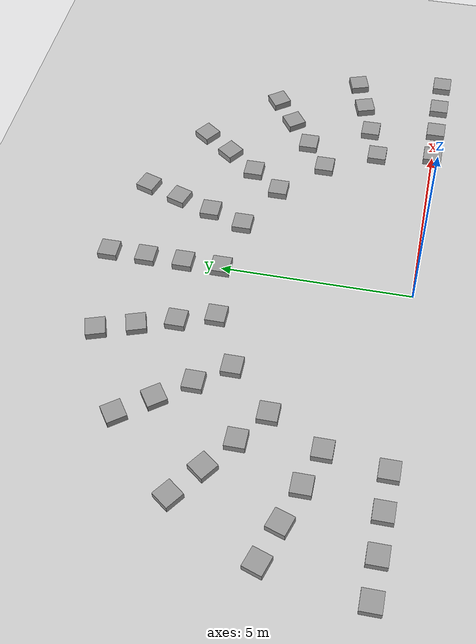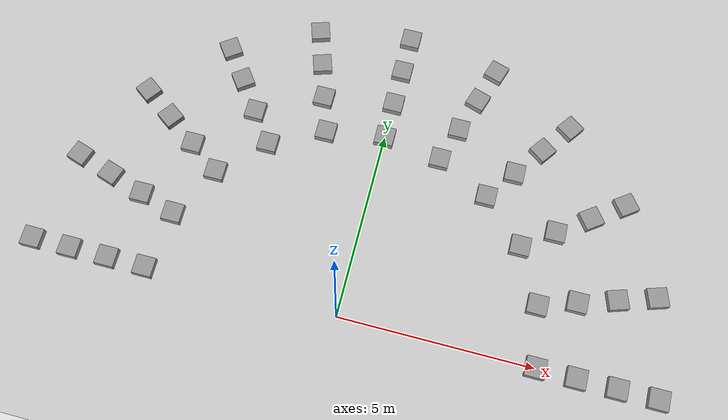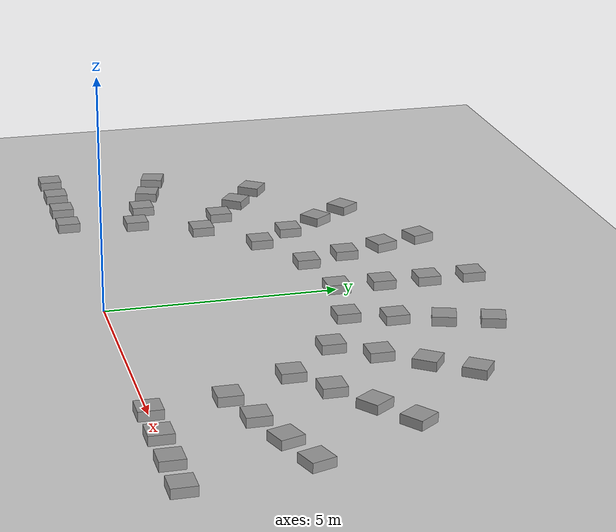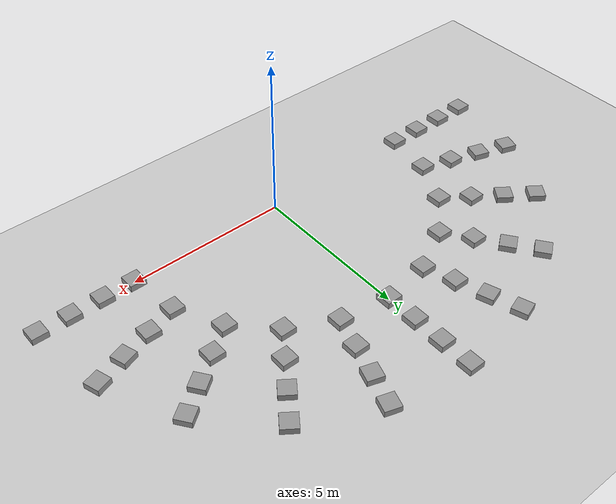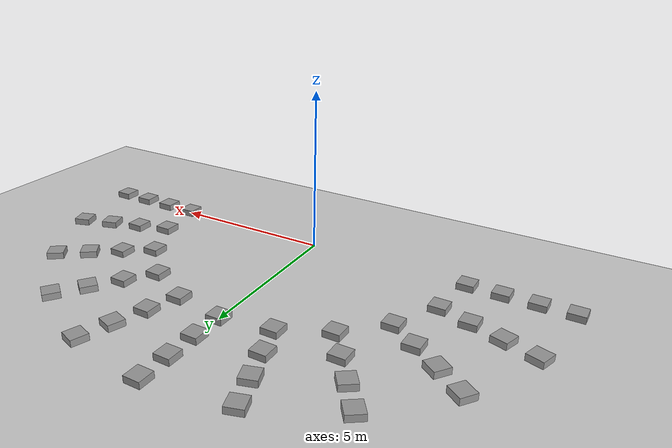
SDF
<sdf version='1.6'>
  <world name='default'>
    <light name='sun' type='directional'>
      <cast_shadows>1</cast_shadows>
      <pose frame=''>0 0 10 0 -0 0</pose>
      <diffuse>0.8 0.8 0.8 1</diffuse>
      <specular>0.1 0.1 0.1 1</specular>
      <attenuation>
        <range>1000</range>
        <constant>0.9</constant>
        <linear>0.01</linear>
        <quadratic>0.001</quadratic>
      </attenuation>
      <direction>-0.5 0.5 -1</direction>
    </light>
    <model name='ground_plane'>
      <static>1</static>
      <link name='link'>
        <collision name='collision'>
          <geometry>
            <plane>
              <normal>0 0 1</normal>
              <size>100 100</size>
            </plane>
          </geometry>
          <surface>
            <friction>
              <ode>
                <mu>100</mu>
                <mu2>50</mu2>
              </ode>
              <torsional>
                <ode/>
              </torsional>
            </friction>
            <contact>
              <ode/>
            </contact>
            <bounce/>
          </surface>
          <max_contacts>10</max_contacts>
        </collision>
        <visual name='visual'>
          <cast_shadows>0</cast_shadows>
          <geometry>
            <plane>
              <normal>0 0 1</normal>
              <size>100 100</size>
            </plane>
          </geometry>
          <material>
            <script>
              <uri>file://media/materials/scripts/gazebo.material</uri>
              <name>Gazebo/Grey</name>
            </script>
          </material>
        </visual>
        <self_collide>0</self_collide>
        <enable_wind>0</enable_wind>
        <kinematic>0</kinematic>
      </link>
    </model>
    <gravity>0 1 -9.81</gravity>
    <magnetic_field>6e-06 2.3e-05 -4.2e-05</magnetic_field>
    <atmosphere type='adiabatic'/>
    <physics name='default_physics' default='0' type='ode'>
      <max_step_size>0.001</max_step_size>
      <real_time_factor>1</real_time_factor>
      <real_time_update_rate>1000</real_time_update_rate>
    </physics>
    <scene>
      <ambient>0.4 0.4 0.4 1</ambient>
      <background>0.7 0.7 0.7 1</background>
      <shadows>1</shadows>
    </scene>
    <audio>
      <device>default</device>
    </audio>
    <wind/>
    <spherical_coordinates>
      <surface_model>EARTH_WGS84</surface_model>
      <latitude_deg>0</latitude_deg>
      <longitude_deg>0</longitude_deg>
      <elevation>0</elevation>
      <heading_deg>0</heading_deg>
    </spherical_coordinates>
    <model name='box_model0'>
      <pose frame=''>5 0 0.1 0 -0 0</pose>
      <link name='link_1'>
        <pose frame=''>0 0 0 0 -0 0</pose>
        <inertial>
          <mass>1</mass>
          <pose frame=''>0 0 0 0 -0 0</pose>
          <inertia>
            <ixx>0.0241667</ixx>
            <ixy>0</ixy>
            <ixz>0</ixz>
            <iyy>0.0241667</iyy>
            <iyz>0</iyz>
            <izz>0.0416667</izz>
          </inertia>
        </inertial>
        <collision name='collision'>
          <geometry>
            <box>
              <size>0.5 0.5 0.2</size>
            </box>
          </geometry>
          <pose frame=''>0 0 0 0 -0 0</pose>
          <surface>
            <friction>
              <ode>
                <mu>100</mu>
                <mu2>0</mu2>
                <fdir1>-0 1 0</fdir1>
              </ode>
              <torsional>
                <ode/>
              </torsional>
            </friction>
            <bounce/>
            <contact>
              <ode/>
              <bullet>
                <split_impulse>1</split_impulse>
                <split_impulse_penetration_threshold>-0.01</split_impulse_penetration_threshold>
              </bullet>
            </contact>
          </surface>
          <max_contacts>10</max_contacts>
        </collision>
        <visual name='visual'>
          <geometry>
            <box>
              <size>0.5 0.5 0.2</size>
            </box>
          </geometry>
          <material>
            <script>
              <name>Gazebo/Grey</name>
              <uri>file://media/materials/scripts/gazebo.material</uri>
            </script>
          </material>
        </visual>
        <self_collide>0</self_collide>
        <enable_wind>0</enable_wind>
        <kinematic>0</kinematic>
      </link>
    </model>
    <model name='box_model1'>
      <pose frame=''>4.75528 1.54509 0.1 0 -0 0</pose>
      <link name='link_1'>
        <pose frame=''>0 0 0 0 -0 0</pose>
        <inertial>
          <mass>1</mass>
          <pose frame=''>0 0 0 0 -0 0</pose>
          <inertia>
            <ixx>0.0241667</ixx>
            <ixy>0</ixy>
            <ixz>0</ixz>
            <iyy>0.0241667</iyy>
            <iyz>0</iyz>
            <izz>0.0416667</izz>
          </inertia>
        </inertial>
        <collision name='collision'>
          <geometry>
            <box>
              <size>0.5 0.5 0.2</size>
            </box>
          </geometry>
          <pose frame=''>0 0 0 0 -0 0</pose>
          <surface>
            <friction>
              <ode>
                <mu>100</mu>
                <mu2>0</mu2>
                <fdir1>-0.309017 0.951057 0</fdir1>
              </ode>
              <torsional>
                <ode/>
              </torsional>
            </friction>
            <bounce/>
            <contact>
              <ode/>
              <bullet>
                <split_impulse>1</split_impulse>
                <split_impulse_penetration_threshold>-0.01</split_impulse_penetration_threshold>
              </bullet>
            </contact>
          </surface>
          <max_contacts>10</max_contacts>
        </collision>
        <visual name='visual'>
          <geometry>
            <box>
              <size>0.5 0.5 0.2</size>
            </box>
          </geometry>
          <material>
            <script>
              <name>Gazebo/Grey</name>
              <uri>file://media/materials/scripts/gazebo.material</uri>
            </script>
          </material>
        </visual>
        <self_collide>0</self_collide>
        <enable_wind>0</enable_wind>
        <kinematic>0</kinematic>
      </link>
    </model>
    <model name='box_model2'>
      <pose frame=''>4.04509 2.93893 0.1 0 -0 0</pose>
      <link name='link_1'>
        <pose frame=''>0 0 0 0 -0 0</pose>
        <inertial>
          <mass>1</mass>
          <pose frame=''>0 0 0 0 -0 0</pose>
          <inertia>
            <ixx>0.0241667</ixx>
            <ixy>0</ixy>
            <ixz>0</ixz>
            <iyy>0.0241667</iyy>
            <iyz>0</iyz>
            <izz>0.0416667</izz>
          </inertia>
        </inertial>
        <collision name='collision'>
          <geometry>
            <box>
              <size>0.5 0.5 0.2</size>
            </box>
          </geometry>
          <pose frame=''>0 0 0 0 -0 0</pose>
          <surface>
            <friction>
              <ode>
                <mu>100</mu>
                <mu2>0</mu2>
                <fdir1>-0.587785 0.809017 0</fdir1>
              </ode>
              <torsional>
                <ode/>
              </torsional>
            </friction>
            <bounce/>
            <contact>
              <ode/>
              <bullet>
                <split_impulse>1</split_impulse>
                <split_impulse_penetration_threshold>-0.01</split_impulse_penetration_threshold>
              </bullet>
            </contact>
          </surface>
          <max_contacts>10</max_contacts>
        </collision>
        <visual name='visual'>
          <geometry>
            <box>
              <size>0.5 0.5 0.2</size>
            </box>
          </geometry>
          <material>
            <script>
              <name>Gazebo/Grey</name>
              <uri>file://media/materials/scripts/gazebo.material</uri>
            </script>
          </material>
        </visual>
        <self_collide>0</self_collide>
        <enable_wind>0</enable_wind>
        <kinematic>0</kinematic>
      </link>
    </model>
    <model name='box_model3'>
      <pose frame=''>2.93893 4.04509 0.1 0 -0 0</pose>
      <link name='link_1'>
        <pose frame=''>0 0 0 0 -0 0</pose>
        <inertial>
          <mass>1</mass>
          <pose frame=''>0 0 0 0 -0 0</pose>
          <inertia>
            <ixx>0.0241667</ixx>
            <ixy>0</ixy>
            <ixz>0</ixz>
            <iyy>0.0241667</iyy>
            <iyz>0</iyz>
            <izz>0.0416667</izz>
          </inertia>
        </inertial>
        <collision name='collision'>
          <geometry>
            <box>
              <size>0.5 0.5 0.2</size>
            </box>
          </geometry>
          <pose frame=''>0 0 0 0 -0 0</pose>
          <surface>
            <friction>
              <ode>
                <mu>100</mu>
                <mu2>0</mu2>
                <fdir1>-0.809017 0.587785 0</fdir1>
              </ode>
              <torsional>
                <ode/>
              </torsional>
            </friction>
            <bounce/>
            <contact>
              <ode/>
              <bullet>
                <split_impulse>1</split_impulse>
                <split_impulse_penetration_threshold>-0.01</split_impulse_penetration_threshold>
              </bullet>
            </contact>
          </surface>
          <max_contacts>10</max_contacts>
        </collision>
        <visual name='visual'>
          <geometry>
            <box>
              <size>0.5 0.5 0.2</size>
            </box>
          </geometry>
          <material>
            <script>
              <name>Gazebo/Grey</name>
              <uri>file://media/materials/scripts/gazebo.material</uri>
            </script>
          </material>
        </visual>
        <self_collide>0</self_collide>
        <enable_wind>0</enable_wind>
        <kinematic>0</kinematic>
      </link>
    </model>
    <model name='box_model4'>
      <pose frame=''>1.54509 4.75528 0.1 0 -0 0</pose>
      <link name='link_1'>
        <pose frame=''>0 0 0 0 -0 0</pose>
        <inertial>
          <mass>1</mass>
          <pose frame=''>0 0 0 0 -0 0</pose>
          <inertia>
            <ixx>0.0241667</ixx>
            <ixy>0</ixy>
            <ixz>0</ixz>
            <iyy>0.0241667</iyy>
            <iyz>0</iyz>
            <izz>0.0416667</izz>
          </inertia>
        </inertial>
        <collision name='collision'>
          <geometry>
            <box>
              <size>0.5 0.5 0.2</size>
            </box>
          </geometry>
          <pose frame=''>0 0 0 0 -0 0</pose>
          <surface>
            <friction>
              <ode>
                <mu>100</mu>
                <mu2>0</mu2>
                <fdir1>-0.951057 0.309017 0</fdir1>
              </ode>
              <torsional>
                <ode/>
              </torsional>
            </friction>
            <bounce/>
            <contact>
              <ode/>
              <bullet>
                <split_impulse>1</split_impulse>
                <split_impulse_penetration_threshold>-0.01</split_impulse_penetration_threshold>
              </bullet>
            </contact>
          </surface>
          <max_contacts>10</max_contacts>
        </collision>
        <visual name='visual'>
          <geometry>
            <box>
              <size>0.5 0.5 0.2</size>
            </box>
          </geometry>
          <material>
            <script>
              <name>Gazebo/Grey</name>
              <uri>file://media/materials/scripts/gazebo.material</uri>
            </script>
          </material>
        </visual>
        <self_collide>0</self_collide>
        <enable_wind>0</enable_wind>
        <kinematic>0</kinematic>
      </link>
    </model>
    <model name='box_model5'>
      <pose frame=''>0 5 0.1 0 -0 0</pose>
      <link name='link_1'>
        <pose frame=''>0 0 0 0 -0 0</pose>
        <inertial>
          <mass>1</mass>
          <pose frame=''>0 0 0 0 -0 0</pose>
          <inertia>
            <ixx>0.0241667</ixx>
            <ixy>0</ixy>
            <ixz>0</ixz>
            <iyy>0.0241667</iyy>
            <iyz>0</iyz>
            <izz>0.0416667</izz>
          </inertia>
        </inertial>
        <collision name='collision'>
          <geometry>
            <box>
              <size>0.5 0.5 0.2</size>
            </box>
          </geometry>
          <pose frame=''>0 0 0 0 -0 0</pose>
          <surface>
            <friction>
              <ode>
                <mu>100</mu>
                <mu2>0</mu2>
                <fdir1>-1 0 0</fdir1>
              </ode>
              <torsional>
                <ode/>
              </torsional>
            </friction>
            <bounce/>
            <contact>
              <ode/>
              <bullet>
                <split_impulse>1</split_impulse>
                <split_impulse_penetration_threshold>-0.01</split_impulse_penetration_threshold>
              </bullet>
            </contact>
          </surface>
          <max_contacts>10</max_contacts>
        </collision>
        <visual name='visual'>
          <geometry>
            <box>
              <size>0.5 0.5 0.2</size>
            </box>
          </geometry>
          <material>
            <script>
              <name>Gazebo/Grey</name>
              <uri>file://media/materials/scripts/gazebo.material</uri>
            </script>
          </material>
        </visual>
        <self_collide>0</self_collide>
        <enable_wind>0</enable_wind>
        <kinematic>0</kinematic>
      </link>
    </model>
    <model name='box_model6'>
      <pose frame=''>-1.54509 4.75528 0.1 0 -0 0</pose>
      <link name='link_1'>
        <pose frame=''>0 0 0 0 -0 0</pose>
        <inertial>
          <mass>1</mass>
          <pose frame=''>0 0 0 0 -0 0</pose>
          <inertia>
            <ixx>0.0241667</ixx>
            <ixy>0</ixy>
            <ixz>0</ixz>
            <iyy>0.0241667</iyy>
            <iyz>0</iyz>
            <izz>0.0416667</izz>
          </inertia>
        </inertial>
        <collision name='collision'>
          <geometry>
            <box>
              <size>0.5 0.5 0.2</size>
            </box>
          </geometry>
          <pose frame=''>0 0 0 0 -0 0</pose>
          <surface>
            <friction>
              <ode>
                <mu>100</mu>
                <mu2>0</mu2>
                <fdir1>-0.951057 -0.309017 0</fdir1>
              </ode>
              <torsional>
                <ode/>
              </torsional>
            </friction>
            <bounce/>
            <contact>
              <ode/>
              <bullet>
                <split_impulse>1</split_impulse>
                <split_impulse_penetration_threshold>-0.01</split_impulse_penetration_threshold>
              </bullet>
            </contact>
          </surface>
          <max_contacts>10</max_contacts>
        </collision>
        <visual name='visual'>
          <geometry>
            <box>
              <size>0.5 0.5 0.2</size>
            </box>
          </geometry>
          <material>
            <script>
              <name>Gazebo/Grey</name>
              <uri>file://media/materials/scripts/gazebo.material</uri>
            </script>
          </material>
        </visual>
        <self_collide>0</self_collide>
        <enable_wind>0</enable_wind>
        <kinematic>0</kinematic>
      </link>
    </model>
    <model name='box_model7'>
      <pose frame=''>-2.93893 4.04509 0.1 0 -0 0</pose>
      <link name='link_1'>
        <pose frame=''>0 0 0 0 -0 0</pose>
        <inertial>
          <mass>1</mass>
          <pose frame=''>0 0 0 0 -0 0</pose>
          <inertia>
            <ixx>0.0241667</ixx>
            <ixy>0</ixy>
            <ixz>0</ixz>
            <iyy>0.0241667</iyy>
            <iyz>0</iyz>
            <izz>0.0416667</izz>
          </inertia>
        </inertial>
        <collision name='collision'>
          <geometry>
            <box>
              <size>0.5 0.5 0.2</size>
            </box>
          </geometry>
          <pose frame=''>0 0 0 0 -0 0</pose>
          <surface>
            <friction>
              <ode>
                <mu>100</mu>
                <mu2>0</mu2>
                <fdir1>-0.809017 -0.587785 0</fdir1>
              </ode>
              <torsional>
                <ode/>
              </torsional>
            </friction>
            <bounce/>
            <contact>
              <ode/>
              <bullet>
                <split_impulse>1</split_impulse>
                <split_impulse_penetration_threshold>-0.01</split_impulse_penetration_threshold>
              </bullet>
            </contact>
          </surface>
          <max_contacts>10</max_contacts>
        </collision>
        <visual name='visual'>
          <geometry>
            <box>
              <size>0.5 0.5 0.2</size>
            </box>
          </geometry>
          <material>
            <script>
              <name>Gazebo/Grey</name>
              <uri>file://media/materials/scripts/gazebo.material</uri>
            </script>
          </material>
        </visual>
        <self_collide>0</self_collide>
        <enable_wind>0</enable_wind>
        <kinematic>0</kinematic>
      </link>
    </model>
    <model name='box_model8'>
      <pose frame=''>-4.04509 2.93893 0.1 0 -0 0</pose>
      <link name='link_1'>
        <pose frame=''>0 0 0 0 -0 0</pose>
        <inertial>
          <mass>1</mass>
          <pose frame=''>0 0 0 0 -0 0</pose>
          <inertia>
            <ixx>0.0241667</ixx>
            <ixy>0</ixy>
            <ixz>0</ixz>
            <iyy>0.0241667</iyy>
            <iyz>0</iyz>
            <izz>0.0416667</izz>
          </inertia>
        </inertial>
        <collision name='collision'>
          <geometry>
            <box>
              <size>0.5 0.5 0.2</size>
            </box>
          </geometry>
          <pose frame=''>0 0 0 0 -0 0</pose>
          <surface>
            <friction>
              <ode>
                <mu>100</mu>
                <mu2>0</mu2>
                <fdir1>-0.587785 -0.809017 0</fdir1>
              </ode>
              <torsional>
                <ode/>
              </torsional>
            </friction>
            <bounce/>
            <contact>
              <ode/>
              <bullet>
                <split_impulse>1</split_impulse>
                <split_impulse_penetration_threshold>-0.01</split_impulse_penetration_threshold>
              </bullet>
            </contact>
          </surface>
          <max_contacts>10</max_contacts>
        </collision>
        <visual name='visual'>
          <geometry>
            <box>
              <size>0.5 0.5 0.2</size>
            </box>
          </geometry>
          <material>
            <script>
              <name>Gazebo/Grey</name>
              <uri>file://media/materials/scripts/gazebo.material</uri>
            </script>
          </material>
        </visual>
        <self_collide>0</self_collide>
        <enable_wind>0</enable_wind>
        <kinematic>0</kinematic>
      </link>
    </model>
    <model name='box_model9'>
      <pose frame=''>-4.75528 1.54509 0.1 0 -0 0</pose>
      <link name='link_1'>
        <pose frame=''>0 0 0 0 -0 0</pose>
        <inertial>
          <mass>1</mass>
          <pose frame=''>0 0 0 0 -0 0</pose>
          <inertia>
            <ixx>0.0241667</ixx>
            <ixy>0</ixy>
            <ixz>0</ixz>
            <iyy>0.0241667</iyy>
            <iyz>0</iyz>
            <izz>0.0416667</izz>
          </inertia>
        </inertial>
        <collision name='collision'>
          <geometry>
            <box>
              <size>0.5 0.5 0.2</size>
            </box>
          </geometry>
          <pose frame=''>0 0 0 0 -0 0</pose>
          <surface>
            <friction>
              <ode>
                <mu>100</mu>
                <mu2>0</mu2>
                <fdir1>-0.309017 -0.951057 0</fdir1>
              </ode>
              <torsional>
                <ode/>
              </torsional>
            </friction>
            <bounce/>
            <contact>
              <ode/>
              <bullet>
                <split_impulse>1</split_impulse>
                <split_impulse_penetration_threshold>-0.01</split_impulse_penetration_threshold>
              </bullet>
            </contact>
          </surface>
          <max_contacts>10</max_contacts>
        </collision>
        <visual name='visual'>
          <geometry>
            <box>
              <size>0.5 0.5 0.2</size>
            </box>
          </geometry>
          <material>
            <script>
              <name>Gazebo/Grey</name>
              <uri>file://media/materials/scripts/gazebo.material</uri>
            </script>
          </material>
        </visual>
        <self_collide>0</self_collide>
        <enable_wind>0</enable_wind>
        <kinematic>0</kinematic>
      </link>
    </model>
    <model name='box_model10'>
      <pose frame=''>-5 0 0.1 0 -0 0</pose>
      <link name='link_1'>
        <pose frame=''>0 0 0 0 -0 0</pose>
        <inertial>
          <mass>1</mass>
          <pose frame=''>0 0 0 0 -0 0</pose>
          <inertia>
            <ixx>0.0241667</ixx>
            <ixy>0</ixy>
            <ixz>0</ixz>
            <iyy>0.0241667</iyy>
            <iyz>0</iyz>
            <izz>0.0416667</izz>
          </inertia>
        </inertial>
        <collision name='collision'>
          <geometry>
            <box>
              <size>0.5 0.5 0.2</size>
            </box>
          </geometry>
          <pose frame=''>0 0 0 0 -0 0</pose>
          <surface>
            <friction>
              <ode>
                <mu>100</mu>
                <mu2>0</mu2>
                <fdir1>-0 -1 0</fdir1>
              </ode>
              <torsional>
                <ode/>
              </torsional>
            </friction>
            <bounce/>
            <contact>
              <ode/>
              <bullet>
                <split_impulse>1</split_impulse>
                <split_impulse_penetration_threshold>-0.01</split_impulse_penetration_threshold>
              </bullet>
            </contact>
          </surface>
          <max_contacts>10</max_contacts>
        </collision>
        <visual name='visual'>
          <geometry>
            <box>
              <size>0.5 0.5 0.2</size>
            </box>
          </geometry>
          <material>
            <script>
              <name>Gazebo/Grey</name>
              <uri>file://media/materials/scripts/gazebo.material</uri>
            </script>
          </material>
        </visual>
        <self_collide>0</self_collide>
        <enable_wind>0</enable_wind>
        <kinematic>0</kinematic>
      </link>
    </model>
    <model name='box_model11'>
      <pose frame=''>6 0 0.1 0 -0 0</pose>
      <link name='link_1'>
        <pose frame=''>0 0 0 0 -0 0</pose>
        <inertial>
          <mass>1</mass>
          <pose frame=''>0 0 0 0 -0 0</pose>
          <inertia>
            <ixx>0.0241667</ixx>
            <ixy>0</ixy>
            <ixz>0</ixz>
            <iyy>0.0241667</iyy>
            <iyz>0</iyz>
            <izz>0.0416667</izz>
          </inertia>
        </inertial>
        <collision name='collision'>
          <geometry>
            <box>
              <size>0.5 0.5 0.2</size>
            </box>
          </geometry>
          <pose frame=''>0 0 0 0 -0 0</pose>
          <surface>
            <friction>
              <ode>
                <mu>100</mu>
                <mu2>0</mu2>
                <fdir1>0 1 0</fdir1>
              </ode>
              <torsional>
                <ode/>
              </torsional>
            </friction>
            <bounce/>
            <contact>
              <ode/>
              <bullet>
                <split_impulse>1</split_impulse>
                <split_impulse_penetration_threshold>-0.01</split_impulse_penetration_threshold>
              </bullet>
            </contact>
          </surface>
          <max_contacts>10</max_contacts>
        </collision>
        <visual name='visual'>
          <geometry>
            <box>
              <size>0.5 0.5 0.2</size>
            </box>
          </geometry>
          <material>
            <script>
              <name>Gazebo/Grey</name>
              <uri>file://media/materials/scripts/gazebo.material</uri>
            </script>
          </material>
        </visual>
        <self_collide>0</self_collide>
        <enable_wind>0</enable_wind>
        <kinematic>0</kinematic>
      </link>
    </model>
    <model name='box_model12'>
      <pose frame=''>5.70634 1.8541 0.1 0 -0 0</pose>
      <link name='link_1'>
        <pose frame=''>0 0 0 0 -0 0</pose>
        <inertial>
          <mass>1</mass>
          <pose frame=''>0 0 0 0 -0 0</pose>
          <inertia>
            <ixx>0.0241667</ixx>
            <ixy>0</ixy>
            <ixz>0</ixz>
            <iyy>0.0241667</iyy>
            <iyz>0</iyz>
            <izz>0.0416667</izz>
          </inertia>
        </inertial>
        <collision name='collision'>
          <geometry>
            <box>
              <size>0.5 0.5 0.2</size>
            </box>
          </geometry>
          <pose frame=''>0 0 0 0 -0 0.314159</pose>
          <surface>
            <friction>
              <ode>
                <mu>100</mu>
                <mu2>0</mu2>
                <fdir1>0 1 0</fdir1>
              </ode>
              <torsional>
                <ode/>
              </torsional>
            </friction>
            <bounce/>
            <contact>
              <ode/>
              <bullet>
                <split_impulse>1</split_impulse>
                <split_impulse_penetration_threshold>-0.01</split_impulse_penetration_threshold>
              </bullet>
            </contact>
          </surface>
          <max_contacts>10</max_contacts>
        </collision>
        <visual name='visual'>
          <geometry>
            <box>
              <size>0.5 0.5 0.2</size>
            </box>
          </geometry>
          <material>
            <script>
              <name>Gazebo/Grey</name>
              <uri>file://media/materials/scripts/gazebo.material</uri>
            </script>
          </material>
        </visual>
        <self_collide>0</self_collide>
        <enable_wind>0</enable_wind>
        <kinematic>0</kinematic>
      </link>
    </model>
    <model name='box_model13'>
      <pose frame=''>4.8541 3.52671 0.1 0 -0 0</pose>
      <link name='link_1'>
        <pose frame=''>0 0 0 0 -0 0</pose>
        <inertial>
          <mass>1</mass>
          <pose frame=''>0 0 0 0 -0 0</pose>
          <inertia>
            <ixx>0.0241667</ixx>
            <ixy>0</ixy>
            <ixz>0</ixz>
            <iyy>0.0241667</iyy>
            <iyz>0</iyz>
            <izz>0.0416667</izz>
          </inertia>
        </inertial>
        <collision name='collision'>
          <geometry>
            <box>
              <size>0.5 0.5 0.2</size>
            </box>
          </geometry>
          <pose frame=''>0 0 0 0 -0 0.628319</pose>
          <surface>
            <friction>
              <ode>
                <mu>100</mu>
                <mu2>0</mu2>
                <fdir1>0 1 0</fdir1>
              </ode>
              <torsional>
                <ode/>
              </torsional>
            </friction>
            <bounce/>
            <contact>
              <ode/>
              <bullet>
                <split_impulse>1</split_impulse>
                <split_impulse_penetration_threshold>-0.01</split_impulse_penetration_threshold>
              </bullet>
            </contact>
          </surface>
          <max_contacts>10</max_contacts>
        </collision>
        <visual name='visual'>
          <geometry>
            <box>
              <size>0.5 0.5 0.2</size>
            </box>
          </geometry>
          <material>
            <script>
              <name>Gazebo/Grey</name>
              <uri>file://media/materials/scripts/gazebo.material</uri>
            </script>
          </material>
        </visual>
        <self_collide>0</self_collide>
        <enable_wind>0</enable_wind>
        <kinematic>0</kinematic>
      </link>
    </model>
    <model name='box_model14'>
      <pose frame=''>3.52671 4.8541 0.1 0 -0 0</pose>
      <link name='link_1'>
        <pose frame=''>0 0 0 0 -0 0</pose>
        <inertial>
          <mass>1</mass>
          <pose frame=''>0 0 0 0 -0 0</pose>
          <inertia>
            <ixx>0.0241667</ixx>
            <ixy>0</ixy>
            <ixz>0</ixz>
            <iyy>0.0241667</iyy>
            <iyz>0</iyz>
            <izz>0.0416667</izz>
          </inertia>
        </inertial>
        <collision name='collision'>
          <geometry>
            <box>
              <size>0.5 0.5 0.2</size>
            </box>
          </geometry>
          <pose frame=''>0 0 0 0 -0 0.942478</pose>
          <surface>
            <friction>
              <ode>
                <mu>100</mu>
                <mu2>0</mu2>
                <fdir1>0 1 0</fdir1>
              </ode>
              <torsional>
                <ode/>
              </torsional>
            </friction>
            <bounce/>
            <contact>
              <ode/>
              <bullet>
                <split_impulse>1</split_impulse>
                <split_impulse_penetration_threshold>-0.01</split_impulse_penetration_threshold>
              </bullet>
            </contact>
          </surface>
          <max_contacts>10</max_contacts>
        </collision>
        <visual name='visual'>
          <geometry>
            <box>
              <size>0.5 0.5 0.2</size>
            </box>
          </geometry>
          <material>
            <script>
              <name>Gazebo/Grey</name>
              <uri>file://media/materials/scripts/gazebo.material</uri>
            </script>
          </material>
        </visual>
        <self_collide>0</self_collide>
        <enable_wind>0</enable_wind>
        <kinematic>0</kinematic>
      </link>
    </model>
    <model name='box_model15'>
      <pose frame=''>1.8541 5.70634 0.1 0 -0 0</pose>
      <link name='link_1'>
        <pose frame=''>0 0 0 0 -0 0</pose>
        <inertial>
          <mass>1</mass>
          <pose frame=''>0 0 0 0 -0 0</pose>
          <inertia>
            <ixx>0.0241667</ixx>
            <ixy>0</ixy>
            <ixz>0</ixz>
            <iyy>0.0241667</iyy>
            <iyz>0</iyz>
            <izz>0.0416667</izz>
          </inertia>
        </inertial>
        <collision name='collision'>
          <geometry>
            <box>
              <size>0.5 0.5 0.2</size>
            </box>
          </geometry>
          <pose frame=''>0 0 0 0 -0 1.25664</pose>
          <surface>
            <friction>
              <ode>
                <mu>100</mu>
                <mu2>0</mu2>
                <fdir1>0 1 0</fdir1>
              </ode>
              <torsional>
                <ode/>
              </torsional>
            </friction>
            <bounce/>
            <contact>
              <ode/>
              <bullet>
                <split_impulse>1</split_impulse>
                <split_impulse_penetration_threshold>-0.01</split_impulse_penetration_threshold>
              </bullet>
            </contact>
          </surface>
          <max_contacts>10</max_contacts>
        </collision>
        <visual name='visual'>
          <geometry>
            <box>
              <size>0.5 0.5 0.2</size>
            </box>
          </geometry>
          <material>
            <script>
              <name>Gazebo/Grey</name>
              <uri>file://media/materials/scripts/gazebo.material</uri>
            </script>
          </material>
        </visual>
        <self_collide>0</self_collide>
        <enable_wind>0</enable_wind>
        <kinematic>0</kinematic>
      </link>
    </model>
    <model name='box_model16'>
      <pose frame=''>0 6 0.1 0 -0 0</pose>
      <link name='link_1'>
        <pose frame=''>0 0 0 0 -0 0</pose>
        <inertial>
          <mass>1</mass>
          <pose frame=''>0 0 0 0 -0 0</pose>
          <inertia>
            <ixx>0.0241667</ixx>
            <ixy>0</ixy>
            <ixz>0</ixz>
            <iyy>0.0241667</iyy>
            <iyz>0</iyz>
            <izz>0.0416667</izz>
          </inertia>
        </inertial>
        <collision name='collision'>
          <geometry>
            <box>
              <size>0.5 0.5 0.2</size>
            </box>
          </geometry>
          <pose frame=''>0 0 0 0 -0 1.5708</pose>
          <surface>
            <friction>
              <ode>
                <mu>100</mu>
                <mu2>0</mu2>
                <fdir1>0 1 0</fdir1>
              </ode>
              <torsional>
                <ode/>
              </torsional>
            </friction>
            <bounce/>
            <contact>
              <ode/>
              <bullet>
                <split_impulse>1</split_impulse>
                <split_impulse_penetration_threshold>-0.01</split_impulse_penetration_threshold>
              </bullet>
            </contact>
          </surface>
          <max_contacts>10</max_contacts>
        </collision>
        <visual name='visual'>
          <geometry>
            <box>
              <size>0.5 0.5 0.2</size>
            </box>
          </geometry>
          <material>
            <script>
              <name>Gazebo/Grey</name>
              <uri>file://media/materials/scripts/gazebo.material</uri>
            </script>
          </material>
        </visual>
        <self_collide>0</self_collide>
        <enable_wind>0</enable_wind>
        <kinematic>0</kinematic>
      </link>
    </model>
    <model name='box_model17'>
      <pose frame=''>-1.8541 5.70634 0.1 0 -0 0</pose>
      <link name='link_1'>
        <pose frame=''>0 0 0 0 -0 0</pose>
        <inertial>
          <mass>1</mass>
          <pose frame=''>0 0 0 0 -0 0</pose>
          <inertia>
            <ixx>0.0241667</ixx>
            <ixy>0</ixy>
            <ixz>0</ixz>
            <iyy>0.0241667</iyy>
            <iyz>0</iyz>
            <izz>0.0416667</izz>
          </inertia>
        </inertial>
        <collision name='collision'>
          <geometry>
            <box>
              <size>0.5 0.5 0.2</size>
            </box>
          </geometry>
          <pose frame=''>0 0 0 0 -0 1.88496</pose>
          <surface>
            <friction>
              <ode>
                <mu>100</mu>
                <mu2>0</mu2>
                <fdir1>0 1 0</fdir1>
              </ode>
              <torsional>
                <ode/>
              </torsional>
            </friction>
            <bounce/>
            <contact>
              <ode/>
              <bullet>
                <split_impulse>1</split_impulse>
                <split_impulse_penetration_threshold>-0.01</split_impulse_penetration_threshold>
              </bullet>
            </contact>
          </surface>
          <max_contacts>10</max_contacts>
        </collision>
        <visual name='visual'>
          <geometry>
            <box>
              <size>0.5 0.5 0.2</size>
            </box>
          </geometry>
          <material>
            <script>
              <name>Gazebo/Grey</name>
              <uri>file://media/materials/scripts/gazebo.material</uri>
            </script>
          </material>
        </visual>
        <self_collide>0</self_collide>
        <enable_wind>0</enable_wind>
        <kinematic>0</kinematic>
      </link>
    </model>
    <model name='box_model18'>
      <pose frame=''>-3.52671 4.8541 0.1 0 -0 0</pose>
      <link name='link_1'>
        <pose frame=''>0 0 0 0 -0 0</pose>
        <inertial>
          <mass>1</mass>
          <pose frame=''>0 0 0 0 -0 0</pose>
          <inertia>
            <ixx>0.0241667</ixx>
            <ixy>0</ixy>
            <ixz>0</ixz>
            <iyy>0.0241667</iyy>
            <iyz>0</iyz>
            <izz>0.0416667</izz>
          </inertia>
        </inertial>
        <collision name='collision'>
          <geometry>
            <box>
              <size>0.5 0.5 0.2</size>
            </box>
          </geometry>
          <pose frame=''>0 0 0 0 -0 2.19911</pose>
          <surface>
            <friction>
              <ode>
                <mu>100</mu>
                <mu2>0</mu2>
                <fdir1>0 1 0</fdir1>
              </ode>
              <torsional>
                <ode/>
              </torsional>
            </friction>
            <bounce/>
            <contact>
              <ode/>
              <bullet>
                <split_impulse>1</split_impulse>
                <split_impulse_penetration_threshold>-0.01</split_impulse_penetration_threshold>
              </bullet>
            </contact>
          </surface>
          <max_contacts>10</max_contacts>
        </collision>
        <visual name='visual'>
          <geometry>
            <box>
              <size>0.5 0.5 0.2</size>
            </box>
          </geometry>
          <material>
            <script>
              <name>Gazebo/Grey</name>
              <uri>file://media/materials/scripts/gazebo.material</uri>
            </script>
          </material>
        </visual>
        <self_collide>0</self_collide>
        <enable_wind>0</enable_wind>
        <kinematic>0</kinematic>
      </link>
    </model>
    <model name='box_model19'>
      <pose frame=''>-4.8541 3.52671 0.1 0 -0 0</pose>
      <link name='link_1'>
        <pose frame=''>0 0 0 0 -0 0</pose>
        <inertial>
          <mass>1</mass>
          <pose frame=''>0 0 0 0 -0 0</pose>
          <inertia>
            <ixx>0.0241667</ixx>
            <ixy>0</ixy>
            <ixz>0</ixz>
            <iyy>0.0241667</iyy>
            <iyz>0</iyz>
            <izz>0.0416667</izz>
          </inertia>
        </inertial>
        <collision name='collision'>
          <geometry>
            <box>
              <size>0.5 0.5 0.2</size>
            </box>
          </geometry>
          <pose frame=''>0 0 0 0 -0 2.51327</pose>
          <surface>
            <friction>
              <ode>
                <mu>100</mu>
                <mu2>0</mu2>
                <fdir1>0 1 0</fdir1>
              </ode>
              <torsional>
                <ode/>
              </torsional>
            </friction>
            <bounce/>
            <contact>
              <ode/>
              <bullet>
                <split_impulse>1</split_impulse>
                <split_impulse_penetration_threshold>-0.01</split_impulse_penetration_threshold>
              </bullet>
            </contact>
          </surface>
          <max_contacts>10</max_contacts>
        </collision>
        <visual name='visual'>
          <geometry>
            <box>
              <size>0.5 0.5 0.2</size>
            </box>
          </geometry>
          <material>
            <script>
              <name>Gazebo/Grey</name>
              <uri>file://media/materials/scripts/gazebo.material</uri>
            </script>
          </material>
        </visual>
        <self_collide>0</self_collide>
        <enable_wind>0</enable_wind>
        <kinematic>0</kinematic>
      </link>
    </model>
    <model name='box_model20'>
      <pose frame=''>-5.70634 1.8541 0.1 0 -0 0</pose>
      <link name='link_1'>
        <pose frame=''>0 0 0 0 -0 0</pose>
        <inertial>
          <mass>1</mass>
          <pose frame=''>0 0 0 0 -0 0</pose>
          <inertia>
            <ixx>0.0241667</ixx>
            <ixy>0</ixy>
            <ixz>0</ixz>
            <iyy>0.0241667</iyy>
            <iyz>0</iyz>
            <izz>0.0416667</izz>
          </inertia>
        </inertial>
        <collision name='collision'>
          <geometry>
            <box>
              <size>0.5 0.5 0.2</size>
            </box>
          </geometry>
          <pose frame=''>0 0 0 0 -0 2.82743</pose>
          <surface>
            <friction>
              <ode>
                <mu>100</mu>
                <mu2>0</mu2>
                <fdir1>0 1 0</fdir1>
              </ode>
              <torsional>
                <ode/>
              </torsional>
            </friction>
            <bounce/>
            <contact>
              <ode/>
              <bullet>
                <split_impulse>1</split_impulse>
                <split_impulse_penetration_threshold>-0.01</split_impulse_penetration_threshold>
              </bullet>
            </contact>
          </surface>
          <max_contacts>10</max_contacts>
        </collision>
        <visual name='visual'>
          <geometry>
            <box>
              <size>0.5 0.5 0.2</size>
            </box>
          </geometry>
          <material>
            <script>
              <name>Gazebo/Grey</name>
              <uri>file://media/materials/scripts/gazebo.material</uri>
            </script>
          </material>
        </visual>
        <self_collide>0</self_collide>
        <enable_wind>0</enable_wind>
        <kinematic>0</kinematic>
      </link>
    </model>
    <model name='box_model21'>
      <pose frame=''>-6 0 0.1 0 -0 0</pose>
      <link name='link_1'>
        <pose frame=''>0 0 0 0 -0 0</pose>
        <inertial>
          <mass>1</mass>
          <pose frame=''>0 0 0 0 -0 0</pose>
          <inertia>
            <ixx>0.0241667</ixx>
            <ixy>0</ixy>
            <ixz>0</ixz>
            <iyy>0.0241667</iyy>
            <iyz>0</iyz>
            <izz>0.0416667</izz>
          </inertia>
        </inertial>
        <collision name='collision'>
          <geometry>
            <box>
              <size>0.5 0.5 0.2</size>
            </box>
          </geometry>
          <pose frame=''>0 0 0 0 -0 3.14159</pose>
          <surface>
            <friction>
              <ode>
                <mu>100</mu>
                <mu2>0</mu2>
                <fdir1>0 1 0</fdir1>
              </ode>
              <torsional>
                <ode/>
              </torsional>
            </friction>
            <bounce/>
            <contact>
              <ode/>
              <bullet>
                <split_impulse>1</split_impulse>
                <split_impulse_penetration_threshold>-0.01</split_impulse_penetration_threshold>
              </bullet>
            </contact>
          </surface>
          <max_contacts>10</max_contacts>
        </collision>
        <visual name='visual'>
          <geometry>
            <box>
              <size>0.5 0.5 0.2</size>
            </box>
          </geometry>
          <material>
            <script>
              <name>Gazebo/Grey</name>
              <uri>file://media/materials/scripts/gazebo.material</uri>
            </script>
          </material>
        </visual>
        <self_collide>0</self_collide>
        <enable_wind>0</enable_wind>
        <kinematic>0</kinematic>
      </link>
    </model>
    <model name='box_model22'>
      <pose frame=''>7 0 0.1 0 -0 0</pose>
      <link name='link_1'>
        <pose frame=''>0 0 0 0 -0 0</pose>
        <inertial>
          <mass>1</mass>
          <pose frame=''>0 0 0 0 -0 0</pose>
          <inertia>
            <ixx>0.0241667</ixx>
            <ixy>0</ixy>
            <ixz>0</ixz>
            <iyy>0.0241667</iyy>
            <iyz>0</iyz>
            <izz>0.0416667</izz>
          </inertia>
        </inertial>
        <collision name='collision'>
          <geometry>
            <box>
              <size>0.5 0.5 0.2</size>
            </box>
          </geometry>
          <pose frame=''>0 0 0 0 -0 0</pose>
          <surface>
            <friction>
              <ode>
                <mu>100</mu>
                <mu2>0</mu2>
                <fdir1>0 1 0</fdir1>
              </ode>
              <torsional>
                <ode/>
              </torsional>
            </friction>
            <bounce/>
            <contact>
              <ode/>
              <bullet>
                <split_impulse>1</split_impulse>
                <split_impulse_penetration_threshold>-0.01</split_impulse_penetration_threshold>
              </bullet>
            </contact>
          </surface>
          <max_contacts>10</max_contacts>
        </collision>
        <visual name='visual'>
          <geometry>
            <box>
              <size>0.5 0.5 0.2</size>
            </box>
          </geometry>
          <material>
            <script>
              <name>Gazebo/Grey</name>
              <uri>file://media/materials/scripts/gazebo.material</uri>
            </script>
          </material>
        </visual>
        <self_collide>0</self_collide>
        <enable_wind>0</enable_wind>
        <kinematic>0</kinematic>
      </link>
    </model>
    <model name='box_model23'>
      <pose frame=''>6.6574 2.16312 0.1 0 -0 0</pose>
      <link name='link_1'>
        <pose frame=''>0 0 0 0 -0 0.314159</pose>
        <inertial>
          <mass>1</mass>
          <pose frame=''>0 0 0 0 -0 0</pose>
          <inertia>
            <ixx>0.0241667</ixx>
            <ixy>0</ixy>
            <ixz>0</ixz>
            <iyy>0.0241667</iyy>
            <iyz>0</iyz>
            <izz>0.0416667</izz>
          </inertia>
        </inertial>
        <collision name='collision'>
          <geometry>
            <box>
              <size>0.5 0.5 0.2</size>
            </box>
          </geometry>
          <pose frame=''>0 0 0 0 -0 0</pose>
          <surface>
            <friction>
              <ode>
                <mu>100</mu>
                <mu2>0</mu2>
                <fdir1>0 1 0</fdir1>
              </ode>
              <torsional>
                <ode/>
              </torsional>
            </friction>
            <bounce/>
            <contact>
              <ode/>
              <bullet>
                <split_impulse>1</split_impulse>
                <split_impulse_penetration_threshold>-0.01</split_impulse_penetration_threshold>
              </bullet>
            </contact>
          </surface>
          <max_contacts>10</max_contacts>
        </collision>
        <visual name='visual'>
          <geometry>
            <box>
              <size>0.5 0.5 0.2</size>
            </box>
          </geometry>
          <material>
            <script>
              <name>Gazebo/Grey</name>
              <uri>file://media/materials/scripts/gazebo.material</uri>
            </script>
          </material>
        </visual>
        <self_collide>0</self_collide>
        <enable_wind>0</enable_wind>
        <kinematic>0</kinematic>
      </link>
    </model>
    <model name='box_model24'>
      <pose frame=''>5.66312 4.1145 0.1 0 -0 0</pose>
      <link name='link_1'>
        <pose frame=''>0 0 0 0 -0 0.628319</pose>
        <inertial>
          <mass>1</mass>
          <pose frame=''>0 0 0 0 -0 0</pose>
          <inertia>
            <ixx>0.0241667</ixx>
            <ixy>0</ixy>
            <ixz>0</ixz>
            <iyy>0.0241667</iyy>
            <iyz>0</iyz>
            <izz>0.0416667</izz>
          </inertia>
        </inertial>
        <collision name='collision'>
          <geometry>
            <box>
              <size>0.5 0.5 0.2</size>
            </box>
          </geometry>
          <pose frame=''>0 0 0 0 -0 0</pose>
          <surface>
            <friction>
              <ode>
                <mu>100</mu>
                <mu2>0</mu2>
                <fdir1>0 1 0</fdir1>
              </ode>
              <torsional>
                <ode/>
              </torsional>
            </friction>
            <bounce/>
            <contact>
              <ode/>
              <bullet>
                <split_impulse>1</split_impulse>
                <split_impulse_penetration_threshold>-0.01</split_impulse_penetration_threshold>
              </bullet>
            </contact>
          </surface>
          <max_contacts>10</max_contacts>
        </collision>
        <visual name='visual'>
          <geometry>
            <box>
              <size>0.5 0.5 0.2</size>
            </box>
          </geometry>
          <material>
            <script>
              <name>Gazebo/Grey</name>
              <uri>file://media/materials/scripts/gazebo.material</uri>
            </script>
          </material>
        </visual>
        <self_collide>0</self_collide>
        <enable_wind>0</enable_wind>
        <kinematic>0</kinematic>
      </link>
    </model>
    <model name='box_model25'>
      <pose frame=''>4.1145 5.66312 0.1 0 -0 0</pose>
      <link name='link_1'>
        <pose frame=''>0 0 0 0 -0 0.942478</pose>
        <inertial>
          <mass>1</mass>
          <pose frame=''>0 0 0 0 -0 0</pose>
          <inertia>
            <ixx>0.0241667</ixx>
            <ixy>0</ixy>
            <ixz>0</ixz>
            <iyy>0.0241667</iyy>
            <iyz>0</iyz>
            <izz>0.0416667</izz>
          </inertia>
        </inertial>
        <collision name='collision'>
          <geometry>
            <box>
              <size>0.5 0.5 0.2</size>
            </box>
          </geometry>
          <pose frame=''>0 0 0 0 -0 0</pose>
          <surface>
            <friction>
              <ode>
                <mu>100</mu>
                <mu2>0</mu2>
                <fdir1>0 1 0</fdir1>
              </ode>
              <torsional>
                <ode/>
              </torsional>
            </friction>
            <bounce/>
            <contact>
              <ode/>
              <bullet>
                <split_impulse>1</split_impulse>
                <split_impulse_penetration_threshold>-0.01</split_impulse_penetration_threshold>
              </bullet>
            </contact>
          </surface>
          <max_contacts>10</max_contacts>
        </collision>
        <visual name='visual'>
          <geometry>
            <box>
              <size>0.5 0.5 0.2</size>
            </box>
          </geometry>
          <material>
            <script>
              <name>Gazebo/Grey</name>
              <uri>file://media/materials/scripts/gazebo.material</uri>
            </script>
          </material>
        </visual>
        <self_collide>0</self_collide>
        <enable_wind>0</enable_wind>
        <kinematic>0</kinematic>
      </link>
    </model>
    <model name='box_model26'>
      <pose frame=''>2.16312 6.6574 0.1 0 -0 0</pose>
      <link name='link_1'>
        <pose frame=''>0 0 0 0 -0 1.25664</pose>
        <inertial>
          <mass>1</mass>
          <pose frame=''>0 0 0 0 -0 0</pose>
          <inertia>
            <ixx>0.0241667</ixx>
            <ixy>0</ixy>
            <ixz>0</ixz>
            <iyy>0.0241667</iyy>
            <iyz>0</iyz>
            <izz>0.0416667</izz>
          </inertia>
        </inertial>
        <collision name='collision'>
          <geometry>
            <box>
              <size>0.5 0.5 0.2</size>
            </box>
          </geometry>
          <pose frame=''>0 0 0 0 -0 0</pose>
          <surface>
            <friction>
              <ode>
                <mu>100</mu>
                <mu2>0</mu2>
                <fdir1>0 1 0</fdir1>
              </ode>
              <torsional>
                <ode/>
              </torsional>
            </friction>
            <bounce/>
            <contact>
              <ode/>
              <bullet>
                <split_impulse>1</split_impulse>
                <split_impulse_penetration_threshold>-0.01</split_impulse_penetration_threshold>
              </bullet>
            </contact>
          </surface>
          <max_contacts>10</max_contacts>
        </collision>
        <visual name='visual'>
          <geometry>
            <box>
              <size>0.5 0.5 0.2</size>
            </box>
          </geometry>
          <material>
            <script>
              <name>Gazebo/Grey</name>
              <uri>file://media/materials/scripts/gazebo.material</uri>
            </script>
          </material>
        </visual>
        <self_collide>0</self_collide>
        <enable_wind>0</enable_wind>
        <kinematic>0</kinematic>
      </link>
    </model>
    <model name='box_model27'>
      <pose frame=''>0 7 0.1 0 -0 0</pose>
      <link name='link_1'>
        <pose frame=''>0 0 0 0 -0 1.5708</pose>
        <inertial>
          <mass>1</mass>
          <pose frame=''>0 0 0 0 -0 0</pose>
          <inertia>
            <ixx>0.0241667</ixx>
            <ixy>0</ixy>
            <ixz>0</ixz>
            <iyy>0.0241667</iyy>
            <iyz>0</iyz>
            <izz>0.0416667</izz>
          </inertia>
        </inertial>
        <collision name='collision'>
          <geometry>
            <box>
              <size>0.5 0.5 0.2</size>
            </box>
          </geometry>
          <pose frame=''>0 0 0 0 -0 0</pose>
          <surface>
            <friction>
              <ode>
                <mu>100</mu>
                <mu2>0</mu2>
                <fdir1>0 1 0</fdir1>
              </ode>
              <torsional>
                <ode/>
              </torsional>
            </friction>
            <bounce/>
            <contact>
              <ode/>
              <bullet>
                <split_impulse>1</split_impulse>
                <split_impulse_penetration_threshold>-0.01</split_impulse_penetration_threshold>
              </bullet>
            </contact>
          </surface>
          <max_contacts>10</max_contacts>
        </collision>
        <visual name='visual'>
          <geometry>
            <box>
              <size>0.5 0.5 0.2</size>
            </box>
          </geometry>
          <material>
            <script>
              <name>Gazebo/Grey</name>
              <uri>file://media/materials/scripts/gazebo.material</uri>
            </script>
          </material>
        </visual>
        <self_collide>0</self_collide>
        <enable_wind>0</enable_wind>
        <kinematic>0</kinematic>
      </link>
    </model>
    <model name='box_model28'>
      <pose frame=''>-2.16312 6.6574 0.1 0 -0 0</pose>
      <link name='link_1'>
        <pose frame=''>0 0 0 0 -0 1.88496</pose>
        <inertial>
          <mass>1</mass>
          <pose frame=''>0 0 0 0 -0 0</pose>
          <inertia>
            <ixx>0.0241667</ixx>
            <ixy>0</ixy>
            <ixz>0</ixz>
            <iyy>0.0241667</iyy>
            <iyz>0</iyz>
            <izz>0.0416667</izz>
          </inertia>
        </inertial>
        <collision name='collision'>
          <geometry>
            <box>
              <size>0.5 0.5 0.2</size>
            </box>
          </geometry>
          <pose frame=''>0 0 0 0 -0 0</pose>
          <surface>
            <friction>
              <ode>
                <mu>100</mu>
                <mu2>0</mu2>
                <fdir1>0 1 0</fdir1>
              </ode>
              <torsional>
                <ode/>
              </torsional>
            </friction>
            <bounce/>
            <contact>
              <ode/>
              <bullet>
                <split_impulse>1</split_impulse>
                <split_impulse_penetration_threshold>-0.01</split_impulse_penetration_threshold>
              </bullet>
            </contact>
          </surface>
          <max_contacts>10</max_contacts>
        </collision>
        <visual name='visual'>
          <geometry>
            <box>
              <size>0.5 0.5 0.2</size>
            </box>
          </geometry>
          <material>
            <script>
              <name>Gazebo/Grey</name>
              <uri>file://media/materials/scripts/gazebo.material</uri>
            </script>
          </material>
        </visual>
        <self_collide>0</self_collide>
        <enable_wind>0</enable_wind>
        <kinematic>0</kinematic>
      </link>
    </model>
    <model name='box_model29'>
      <pose frame=''>-4.1145 5.66312 0.1 0 -0 0</pose>
      <link name='link_1'>
        <pose frame=''>0 0 0 0 -0 2.19911</pose>
        <inertial>
          <mass>1</mass>
          <pose frame=''>0 0 0 0 -0 0</pose>
          <inertia>
            <ixx>0.0241667</ixx>
            <ixy>0</ixy>
            <ixz>0</ixz>
            <iyy>0.0241667</iyy>
            <iyz>0</iyz>
            <izz>0.0416667</izz>
          </inertia>
        </inertial>
        <collision name='collision'>
          <geometry>
            <box>
              <size>0.5 0.5 0.2</size>
            </box>
          </geometry>
          <pose frame=''>0 0 0 0 -0 0</pose>
          <surface>
            <friction>
              <ode>
                <mu>100</mu>
                <mu2>0</mu2>
                <fdir1>0 1 0</fdir1>
              </ode>
              <torsional>
                <ode/>
              </torsional>
            </friction>
            <bounce/>
            <contact>
              <ode/>
              <bullet>
                <split_impulse>1</split_impulse>
                <split_impulse_penetration_threshold>-0.01</split_impulse_penetration_threshold>
              </bullet>
            </contact>
          </surface>
          <max_contacts>10</max_contacts>
        </collision>
        <visual name='visual'>
          <geometry>
            <box>
              <size>0.5 0.5 0.2</size>
            </box>
          </geometry>
          <material>
            <script>
              <name>Gazebo/Grey</name>
              <uri>file://media/materials/scripts/gazebo.material</uri>
            </script>
          </material>
        </visual>
        <self_collide>0</self_collide>
        <enable_wind>0</enable_wind>
        <kinematic>0</kinematic>
      </link>
    </model>
    <model name='box_model30'>
      <pose frame=''>-5.66312 4.1145 0.1 0 -0 0</pose>
      <link name='link_1'>
        <pose frame=''>0 0 0 0 -0 2.51327</pose>
        <inertial>
          <mass>1</mass>
          <pose frame=''>0 0 0 0 -0 0</pose>
          <inertia>
            <ixx>0.0241667</ixx>
            <ixy>0</ixy>
            <ixz>0</ixz>
            <iyy>0.0241667</iyy>
            <iyz>0</iyz>
            <izz>0.0416667</izz>
          </inertia>
        </inertial>
        <collision name='collision'>
          <geometry>
            <box>
              <size>0.5 0.5 0.2</size>
            </box>
          </geometry>
          <pose frame=''>0 0 0 0 -0 0</pose>
          <surface>
            <friction>
              <ode>
                <mu>100</mu>
                <mu2>0</mu2>
                <fdir1>0 1 0</fdir1>
              </ode>
              <torsional>
                <ode/>
              </torsional>
            </friction>
            <bounce/>
            <contact>
              <ode/>
              <bullet>
                <split_impulse>1</split_impulse>
                <split_impulse_penetration_threshold>-0.01</split_impulse_penetration_threshold>
              </bullet>
            </contact>
          </surface>
          <max_contacts>10</max_contacts>
        </collision>
        <visual name='visual'>
          <geometry>
            <box>
              <size>0.5 0.5 0.2</size>
            </box>
          </geometry>
          <material>
            <script>
              <name>Gazebo/Grey</name>
              <uri>file://media/materials/scripts/gazebo.material</uri>
            </script>
          </material>
        </visual>
        <self_collide>0</self_collide>
        <enable_wind>0</enable_wind>
        <kinematic>0</kinematic>
      </link>
    </model>
    <model name='box_model31'>
      <pose frame=''>-6.6574 2.16312 0.1 0 -0 0</pose>
      <link name='link_1'>
        <pose frame=''>0 0 0 0 -0 2.82743</pose>
        <inertial>
          <mass>1</mass>
          <pose frame=''>0 0 0 0 -0 0</pose>
          <inertia>
            <ixx>0.0241667</ixx>
            <ixy>0</ixy>
            <ixz>0</ixz>
            <iyy>0.0241667</iyy>
            <iyz>0</iyz>
            <izz>0.0416667</izz>
          </inertia>
        </inertial>
        <collision name='collision'>
          <geometry>
            <box>
              <size>0.5 0.5 0.2</size>
            </box>
          </geometry>
          <pose frame=''>0 0 0 0 -0 0</pose>
          <surface>
            <friction>
              <ode>
                <mu>100</mu>
                <mu2>0</mu2>
                <fdir1>0 1 0</fdir1>
              </ode>
              <torsional>
                <ode/>
              </torsional>
            </friction>
            <bounce/>
            <contact>
              <ode/>
              <bullet>
                <split_impulse>1</split_impulse>
                <split_impulse_penetration_threshold>-0.01</split_impulse_penetration_threshold>
              </bullet>
            </contact>
          </surface>
          <max_contacts>10</max_contacts>
        </collision>
        <visual name='visual'>
          <geometry>
            <box>
              <size>0.5 0.5 0.2</size>
            </box>
          </geometry>
          <material>
            <script>
              <name>Gazebo/Grey</name>
              <uri>file://media/materials/scripts/gazebo.material</uri>
            </script>
          </material>
        </visual>
        <self_collide>0</self_collide>
        <enable_wind>0</enable_wind>
        <kinematic>0</kinematic>
      </link>
    </model>
    <model name='box_model32'>
      <pose frame=''>-7 0 0.1 0 -0 0</pose>
      <link name='link_1'>
        <pose frame=''>0 0 0 0 -0 3.14159</pose>
        <inertial>
          <mass>1</mass>
          <pose frame=''>0 0 0 0 -0 0</pose>
          <inertia>
            <ixx>0.0241667</ixx>
            <ixy>0</ixy>
            <ixz>0</ixz>
            <iyy>0.0241667</iyy>
            <iyz>0</iyz>
            <izz>0.0416667</izz>
          </inertia>
        </inertial>
        <collision name='collision'>
          <geometry>
            <box>
              <size>0.5 0.5 0.2</size>
            </box>
          </geometry>
          <pose frame=''>0 0 0 0 -0 0</pose>
          <surface>
            <friction>
              <ode>
                <mu>100</mu>
                <mu2>0</mu2>
                <fdir1>0 1 0</fdir1>
              </ode>
              <torsional>
                <ode/>
              </torsional>
            </friction>
            <bounce/>
            <contact>
              <ode/>
              <bullet>
                <split_impulse>1</split_impulse>
                <split_impulse_penetration_threshold>-0.01</split_impulse_penetration_threshold>
              </bullet>
            </contact>
          </surface>
          <max_contacts>10</max_contacts>
        </collision>
        <visual name='visual'>
          <geometry>
            <box>
              <size>0.5 0.5 0.2</size>
            </box>
          </geometry>
          <material>
            <script>
              <name>Gazebo/Grey</name>
              <uri>file://media/materials/scripts/gazebo.material</uri>
            </script>
          </material>
        </visual>
        <self_collide>0</self_collide>
        <enable_wind>0</enable_wind>
        <kinematic>0</kinematic>
      </link>
    </model>
    <model name='box_model33'>
      <pose frame=''>8 0 0.1 0 -0 0</pose>
      <link name='link_1'>
        <pose frame=''>0 0 0 0 -0 0</pose>
        <inertial>
          <mass>1</mass>
          <pose frame=''>0 0 0 0 -0 0</pose>
          <inertia>
            <ixx>0.0241667</ixx>
            <ixy>0</ixy>
            <ixz>0</ixz>
            <iyy>0.0241667</iyy>
            <iyz>0</iyz>
            <izz>0.0416667</izz>
          </inertia>
        </inertial>
        <collision name='collision'>
          <geometry>
            <box>
              <size>0.5 0.5 0.2</size>
            </box>
          </geometry>
          <pose frame=''>0 0 0 0 -0 0</pose>
          <surface>
            <friction>
              <ode>
                <mu>100</mu>
                <mu2>0</mu2>
                <fdir1>0 1 0</fdir1>
              </ode>
              <torsional>
                <ode/>
              </torsional>
            </friction>
            <bounce/>
            <contact>
              <ode/>
              <bullet>
                <split_impulse>1</split_impulse>
                <split_impulse_penetration_threshold>-0.01</split_impulse_penetration_threshold>
              </bullet>
            </contact>
          </surface>
          <max_contacts>10</max_contacts>
        </collision>
        <visual name='visual'>
          <geometry>
            <box>
              <size>0.5 0.5 0.2</size>
            </box>
          </geometry>
          <material>
            <script>
              <name>Gazebo/Grey</name>
              <uri>file://media/materials/scripts/gazebo.material</uri>
            </script>
          </material>
        </visual>
        <self_collide>0</self_collide>
        <enable_wind>0</enable_wind>
        <kinematic>0</kinematic>
      </link>
    </model>
    <model name='box_model34'>
      <pose frame=''>7.60845 2.47214 0.1 0 -0 0.314159</pose>
      <link name='link_1'>
        <pose frame=''>0 0 0 0 -0 0</pose>
        <inertial>
          <mass>1</mass>
          <pose frame=''>0 0 0 0 -0 0</pose>
          <inertia>
            <ixx>0.0241667</ixx>
            <ixy>0</ixy>
            <ixz>0</ixz>
            <iyy>0.0241667</iyy>
            <iyz>0</iyz>
            <izz>0.0416667</izz>
          </inertia>
        </inertial>
        <collision name='collision'>
          <geometry>
            <box>
              <size>0.5 0.5 0.2</size>
            </box>
          </geometry>
          <pose frame=''>0 0 0 0 -0 0</pose>
          <surface>
            <friction>
              <ode>
                <mu>100</mu>
                <mu2>0</mu2>
                <fdir1>0 1 0</fdir1>
              </ode>
              <torsional>
                <ode/>
              </torsional>
            </friction>
            <bounce/>
            <contact>
              <ode/>
              <bullet>
                <split_impulse>1</split_impulse>
                <split_impulse_penetration_threshold>-0.01</split_impulse_penetration_threshold>
              </bullet>
            </contact>
          </surface>
          <max_contacts>10</max_contacts>
        </collision>
        <visual name='visual'>
          <geometry>
            <box>
              <size>0.5 0.5 0.2</size>
            </box>
          </geometry>
          <material>
            <script>
              <name>Gazebo/Grey</name>
              <uri>file://media/materials/scripts/gazebo.material</uri>
            </script>
          </material>
        </visual>
        <self_collide>0</self_collide>
        <enable_wind>0</enable_wind>
        <kinematic>0</kinematic>
      </link>
    </model>
    <model name='box_model35'>
      <pose frame=''>6.47214 4.70228 0.1 0 -0 0.628319</pose>
      <link name='link_1'>
        <pose frame=''>0 0 0 0 -0 0</pose>
        <inertial>
          <mass>1</mass>
          <pose frame=''>0 0 0 0 -0 0</pose>
          <inertia>
            <ixx>0.0241667</ixx>
            <ixy>0</ixy>
            <ixz>0</ixz>
            <iyy>0.0241667</iyy>
            <iyz>0</iyz>
            <izz>0.0416667</izz>
          </inertia>
        </inertial>
        <collision name='collision'>
          <geometry>
            <box>
              <size>0.5 0.5 0.2</size>
            </box>
          </geometry>
          <pose frame=''>0 0 0 0 -0 0</pose>
          <surface>
            <friction>
              <ode>
                <mu>100</mu>
                <mu2>0</mu2>
                <fdir1>0 1 0</fdir1>
              </ode>
              <torsional>
                <ode/>
              </torsional>
            </friction>
            <bounce/>
            <contact>
              <ode/>
              <bullet>
                <split_impulse>1</split_impulse>
                <split_impulse_penetration_threshold>-0.01</split_impulse_penetration_threshold>
              </bullet>
            </contact>
          </surface>
          <max_contacts>10</max_contacts>
        </collision>
        <visual name='visual'>
          <geometry>
            <box>
              <size>0.5 0.5 0.2</size>
            </box>
          </geometry>
          <material>
            <script>
              <name>Gazebo/Grey</name>
              <uri>file://media/materials/scripts/gazebo.material</uri>
            </script>
          </material>
        </visual>
        <self_collide>0</self_collide>
        <enable_wind>0</enable_wind>
        <kinematic>0</kinematic>
      </link>
    </model>
    <model name='box_model36'>
      <pose frame=''>4.70228 6.47214 0.1 0 -0 0.942478</pose>
      <link name='link_1'>
        <pose frame=''>0 0 0 0 -0 0</pose>
        <inertial>
          <mass>1</mass>
          <pose frame=''>0 0 0 0 -0 0</pose>
          <inertia>
            <ixx>0.0241667</ixx>
            <ixy>0</ixy>
            <ixz>0</ixz>
            <iyy>0.0241667</iyy>
            <iyz>0</iyz>
            <izz>0.0416667</izz>
          </inertia>
        </inertial>
        <collision name='collision'>
          <geometry>
            <box>
              <size>0.5 0.5 0.2</size>
            </box>
          </geometry>
          <pose frame=''>0 0 0 0 -0 0</pose>
          <surface>
            <friction>
              <ode>
                <mu>100</mu>
                <mu2>0</mu2>
                <fdir1>0 1 0</fdir1>
              </ode>
              <torsional>
                <ode/>
              </torsional>
            </friction>
            <bounce/>
            <contact>
              <ode/>
              <bullet>
                <split_impulse>1</split_impulse>
                <split_impulse_penetration_threshold>-0.01</split_impulse_penetration_threshold>
              </bullet>
            </contact>
          </surface>
          <max_contacts>10</max_contacts>
        </collision>
        <visual name='visual'>
          <geometry>
            <box>
              <size>0.5 0.5 0.2</size>
            </box>
          </geometry>
          <material>
            <script>
              <name>Gazebo/Grey</name>
              <uri>file://media/materials/scripts/gazebo.material</uri>
            </script>
          </material>
        </visual>
        <self_collide>0</self_collide>
        <enable_wind>0</enable_wind>
        <kinematic>0</kinematic>
      </link>
    </model>
    <model name='box_model37'>
      <pose frame=''>2.47214 7.60845 0.1 0 -0 1.25664</pose>
      <link name='link_1'>
        <pose frame=''>0 0 0 0 -0 0</pose>
        <inertial>
          <mass>1</mass>
          <pose frame=''>0 0 0 0 -0 0</pose>
          <inertia>
            <ixx>0.0241667</ixx>
            <ixy>0</ixy>
            <ixz>0</ixz>
            <iyy>0.0241667</iyy>
            <iyz>0</iyz>
            <izz>0.0416667</izz>
          </inertia>
        </inertial>
        <collision name='collision'>
          <geometry>
            <box>
              <size>0.5 0.5 0.2</size>
            </box>
          </geometry>
          <pose frame=''>0 0 0 0 -0 0</pose>
          <surface>
            <friction>
              <ode>
                <mu>100</mu>
                <mu2>0</mu2>
                <fdir1>0 1 0</fdir1>
              </ode>
              <torsional>
                <ode/>
              </torsional>
            </friction>
            <bounce/>
            <contact>
              <ode/>
              <bullet>
                <split_impulse>1</split_impulse>
                <split_impulse_penetration_threshold>-0.01</split_impulse_penetration_threshold>
              </bullet>
            </contact>
          </surface>
          <max_contacts>10</max_contacts>
        </collision>
        <visual name='visual'>
          <geometry>
            <box>
              <size>0.5 0.5 0.2</size>
            </box>
          </geometry>
          <material>
            <script>
              <name>Gazebo/Grey</name>
              <uri>file://media/materials/scripts/gazebo.material</uri>
            </script>
          </material>
        </visual>
        <self_collide>0</self_collide>
        <enable_wind>0</enable_wind>
        <kinematic>0</kinematic>
      </link>
    </model>
    <model name='box_model38'>
      <pose frame=''>0 8 0.1 0 -0 1.5708</pose>
      <link name='link_1'>
        <pose frame=''>0 0 0 0 -0 0</pose>
        <inertial>
          <mass>1</mass>
          <pose frame=''>0 0 0 0 -0 0</pose>
          <inertia>
            <ixx>0.0241667</ixx>
            <ixy>0</ixy>
            <ixz>0</ixz>
            <iyy>0.0241667</iyy>
            <iyz>0</iyz>
            <izz>0.0416667</izz>
          </inertia>
        </inertial>
        <collision name='collision'>
          <geometry>
            <box>
              <size>0.5 0.5 0.2</size>
            </box>
          </geometry>
          <pose frame=''>0 0 0 0 -0 0</pose>
          <surface>
            <friction>
              <ode>
                <mu>100</mu>
                <mu2>0</mu2>
                <fdir1>0 1 0</fdir1>
              </ode>
              <torsional>
                <ode/>
              </torsional>
            </friction>
            <bounce/>
            <contact>
              <ode/>
              <bullet>
                <split_impulse>1</split_impulse>
                <split_impulse_penetration_threshold>-0.01</split_impulse_penetration_threshold>
              </bullet>
            </contact>
          </surface>
          <max_contacts>10</max_contacts>
        </collision>
        <visual name='visual'>
          <geometry>
            <box>
              <size>0.5 0.5 0.2</size>
            </box>
          </geometry>
          <material>
            <script>
              <name>Gazebo/Grey</name>
              <uri>file://media/materials/scripts/gazebo.material</uri>
            </script>
          </material>
        </visual>
        <self_collide>0</self_collide>
        <enable_wind>0</enable_wind>
        <kinematic>0</kinematic>
      </link>
    </model>
    <model name='box_model39'>
      <pose frame=''>-2.47214 7.60845 0.1 0 -0 1.88496</pose>
      <link name='link_1'>
        <pose frame=''>0 0 0 0 -0 0</pose>
        <inertial>
          <mass>1</mass>
          <pose frame=''>0 0 0 0 -0 0</pose>
          <inertia>
            <ixx>0.0241667</ixx>
            <ixy>0</ixy>
            <ixz>0</ixz>
            <iyy>0.0241667</iyy>
            <iyz>0</iyz>
            <izz>0.0416667</izz>
          </inertia>
        </inertial>
        <collision name='collision'>
          <geometry>
            <box>
              <size>0.5 0.5 0.2</size>
            </box>
          </geometry>
          <pose frame=''>0 0 0 0 -0 0</pose>
          <surface>
            <friction>
              <ode>
                <mu>100</mu>
                <mu2>0</mu2>
                <fdir1>0 1 0</fdir1>
              </ode>
              <torsional>
                <ode/>
              </torsional>
            </friction>
            <bounce/>
            <contact>
              <ode/>
              <bullet>
                <split_impulse>1</split_impulse>
                <split_impulse_penetration_threshold>-0.01</split_impulse_penetration_threshold>
              </bullet>
            </contact>
          </surface>
          <max_contacts>10</max_contacts>
        </collision>
        <visual name='visual'>
          <geometry>
            <box>
              <size>0.5 0.5 0.2</size>
            </box>
          </geometry>
          <material>
            <script>
              <name>Gazebo/Grey</name>
              <uri>file://media/materials/scripts/gazebo.material</uri>
            </script>
          </material>
        </visual>
        <self_collide>0</self_collide>
        <enable_wind>0</enable_wind>
        <kinematic>0</kinematic>
      </link>
    </model>
    <model name='box_model40'>
      <pose frame=''>-4.70228 6.47214 0.1 0 -0 2.19911</pose>
      <link name='link_1'>
        <pose frame=''>0 0 0 0 -0 0</pose>
        <inertial>
          <mass>1</mass>
          <pose frame=''>0 0 0 0 -0 0</pose>
          <inertia>
            <ixx>0.0241667</ixx>
            <ixy>0</ixy>
            <ixz>0</ixz>
            <iyy>0.0241667</iyy>
            <iyz>0</iyz>
            <izz>0.0416667</izz>
          </inertia>
        </inertial>
        <collision name='collision'>
          <geometry>
            <box>
              <size>0.5 0.5 0.2</size>
            </box>
          </geometry>
          <pose frame=''>0 0 0 0 -0 0</pose>
          <surface>
            <friction>
              <ode>
                <mu>100</mu>
                <mu2>0</mu2>
                <fdir1>0 1 0</fdir1>
              </ode>
              <torsional>
                <ode/>
              </torsional>
            </friction>
            <bounce/>
            <contact>
              <ode/>
              <bullet>
                <split_impulse>1</split_impulse>
                <split_impulse_penetration_threshold>-0.01</split_impulse_penetration_threshold>
              </bullet>
            </contact>
          </surface>
          <max_contacts>10</max_contacts>
        </collision>
        <visual name='visual'>
          <geometry>
            <box>
              <size>0.5 0.5 0.2</size>
            </box>
          </geometry>
          <material>
            <script>
              <name>Gazebo/Grey</name>
              <uri>file://media/materials/scripts/gazebo.material</uri>
            </script>
          </material>
        </visual>
        <self_collide>0</self_collide>
        <enable_wind>0</enable_wind>
        <kinematic>0</kinematic>
      </link>
    </model>
    <model name='box_model41'>
      <pose frame=''>-6.47214 4.70228 0.1 0 -0 2.51327</pose>
      <link name='link_1'>
        <pose frame=''>0 0 0 0 -0 0</pose>
        <inertial>
          <mass>1</mass>
          <pose frame=''>0 0 0 0 -0 0</pose>
          <inertia>
            <ixx>0.0241667</ixx>
            <ixy>0</ixy>
            <ixz>0</ixz>
            <iyy>0.0241667</iyy>
            <iyz>0</iyz>
            <izz>0.0416667</izz>
          </inertia>
        </inertial>
        <collision name='collision'>
          <geometry>
            <box>
              <size>0.5 0.5 0.2</size>
            </box>
          </geometry>
          <pose frame=''>0 0 0 0 -0 0</pose>
          <surface>
            <friction>
              <ode>
                <mu>100</mu>
                <mu2>0</mu2>
                <fdir1>0 1 0</fdir1>
              </ode>
              <torsional>
                <ode/>
              </torsional>
            </friction>
            <bounce/>
            <contact>
              <ode/>
              <bullet>
                <split_impulse>1</split_impulse>
                <split_impulse_penetration_threshold>-0.01</split_impulse_penetration_threshold>
              </bullet>
            </contact>
          </surface>
          <max_contacts>10</max_contacts>
        </collision>
        <visual name='visual'>
          <geometry>
            <box>
              <size>0.5 0.5 0.2</size>
            </box>
          </geometry>
          <material>
            <script>
              <name>Gazebo/Grey</name>
              <uri>file://media/materials/scripts/gazebo.material</uri>
            </script>
          </material>
        </visual>
        <self_collide>0</self_collide>
        <enable_wind>0</enable_wind>
        <kinematic>0</kinematic>
      </link>
    </model>
    <model name='box_model42'>
      <pose frame=''>-7.60845 2.47214 0.1 0 -0 2.82743</pose>
      <link name='link_1'>
        <pose frame=''>0 0 0 0 -0 0</pose>
        <inertial>
          <mass>1</mass>
          <pose frame=''>0 0 0 0 -0 0</pose>
          <inertia>
            <ixx>0.0241667</ixx>
            <ixy>0</ixy>
            <ixz>0</ixz>
            <iyy>0.0241667</iyy>
            <iyz>0</iyz>
            <izz>0.0416667</izz>
          </inertia>
        </inertial>
        <collision name='collision'>
          <geometry>
            <box>
              <size>0.5 0.5 0.2</size>
            </box>
          </geometry>
          <pose frame=''>0 0 0 0 -0 0</pose>
          <surface>
            <friction>
              <ode>
                <mu>100</mu>
                <mu2>0</mu2>
                <fdir1>0 1 0</fdir1>
              </ode>
              <torsional>
                <ode/>
              </torsional>
            </friction>
            <bounce/>
            <contact>
              <ode/>
              <bullet>
                <split_impulse>1</split_impulse>
                <split_impulse_penetration_threshold>-0.01</split_impulse_penetration_threshold>
              </bullet>
            </contact>
          </surface>
          <max_contacts>10</max_contacts>
        </collision>
        <visual name='visual'>
          <geometry>
            <box>
              <size>0.5 0.5 0.2</size>
            </box>
          </geometry>
          <material>
            <script>
              <name>Gazebo/Grey</name>
              <uri>file://media/materials/scripts/gazebo.material</uri>
            </script>
          </material>
        </visual>
        <self_collide>0</self_collide>
        <enable_wind>0</enable_wind>
        <kinematic>0</kinematic>
      </link>
    </model>
    <model name='box_model43'>
      <pose frame=''>-8 0 0.1 0 -0 3.14159</pose>
      <link name='link_1'>
        <pose frame=''>0 0 0 0 -0 0</pose>
        <inertial>
          <mass>1</mass>
          <pose frame=''>0 0 0 0 -0 0</pose>
          <inertia>
            <ixx>0.0241667</ixx>
            <ixy>0</ixy>
            <ixz>0</ixz>
            <iyy>0.0241667</iyy>
            <iyz>0</iyz>
            <izz>0.0416667</izz>
          </inertia>
        </inertial>
        <collision name='collision'>
          <geometry>
            <box>
              <size>0.5 0.5 0.2</size>
            </box>
          </geometry>
          <pose frame=''>0 0 0 0 -0 0</pose>
          <surface>
            <friction>
              <ode>
                <mu>100</mu>
                <mu2>0</mu2>
                <fdir1>0 1 0</fdir1>
              </ode>
              <torsional>
                <ode/>
              </torsional>
            </friction>
            <bounce/>
            <contact>
              <ode/>
              <bullet>
                <split_impulse>1</split_impulse>
                <split_impulse_penetration_threshold>-0.01</split_impulse_penetration_threshold>
              </bullet>
            </contact>
          </surface>
          <max_contacts>10</max_contacts>
        </collision>
        <visual name='visual'>
          <geometry>
            <box>
              <size>0.5 0.5 0.2</size>
            </box>
          </geometry>
          <material>
            <script>
              <name>Gazebo/Grey</name>
              <uri>file://media/materials/scripts/gazebo.material</uri>
            </script>
          </material>
        </visual>
        <self_collide>0</self_collide>
        <enable_wind>0</enable_wind>
        <kinematic>0</kinematic>
      </link>
    </model>
    <gui fullscreen='0'>
      <camera name='user_camera'>
        <pose frame=''>5 -5 2 0 0.275643 2.35619</pose>
        <view_controller>orbit</view_controller>
        <projection_type>perspective</projection_type>
      </camera>
    </gui>
  </world>
</sdf>
